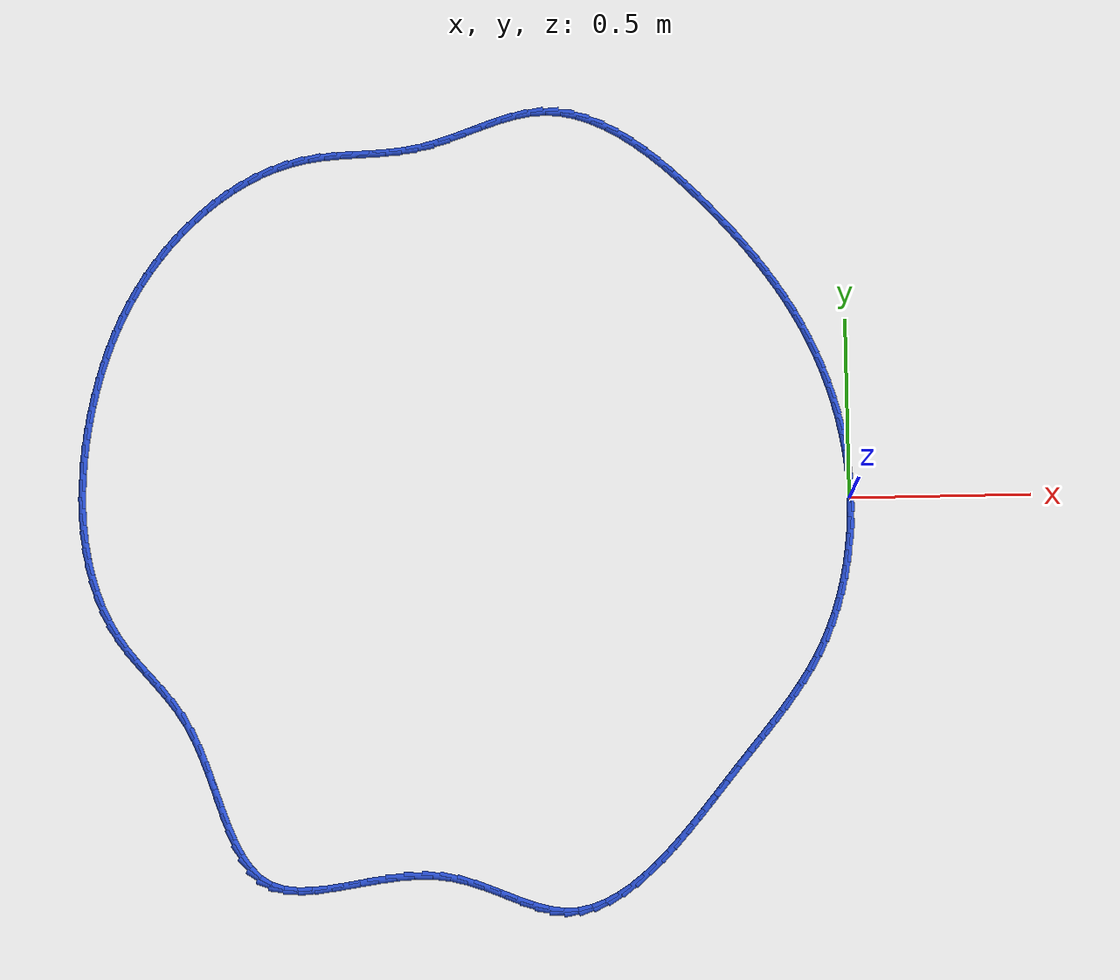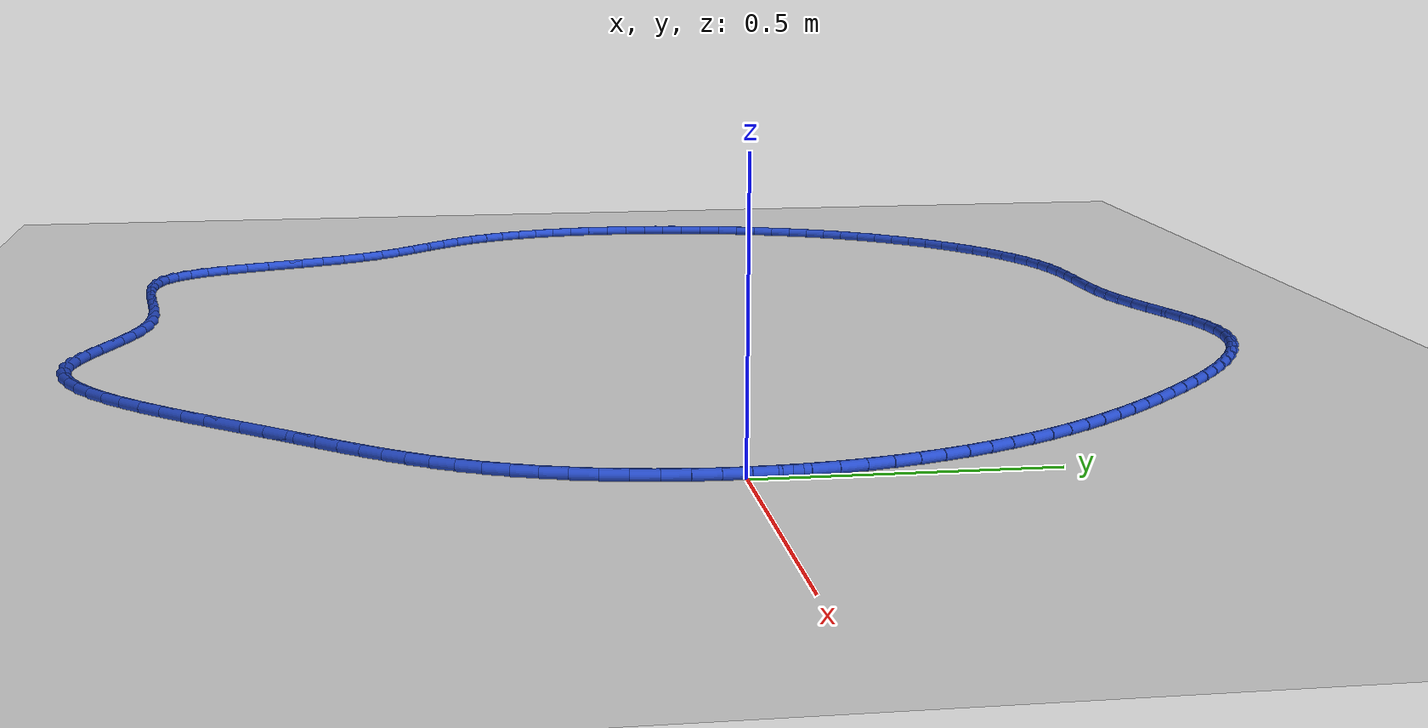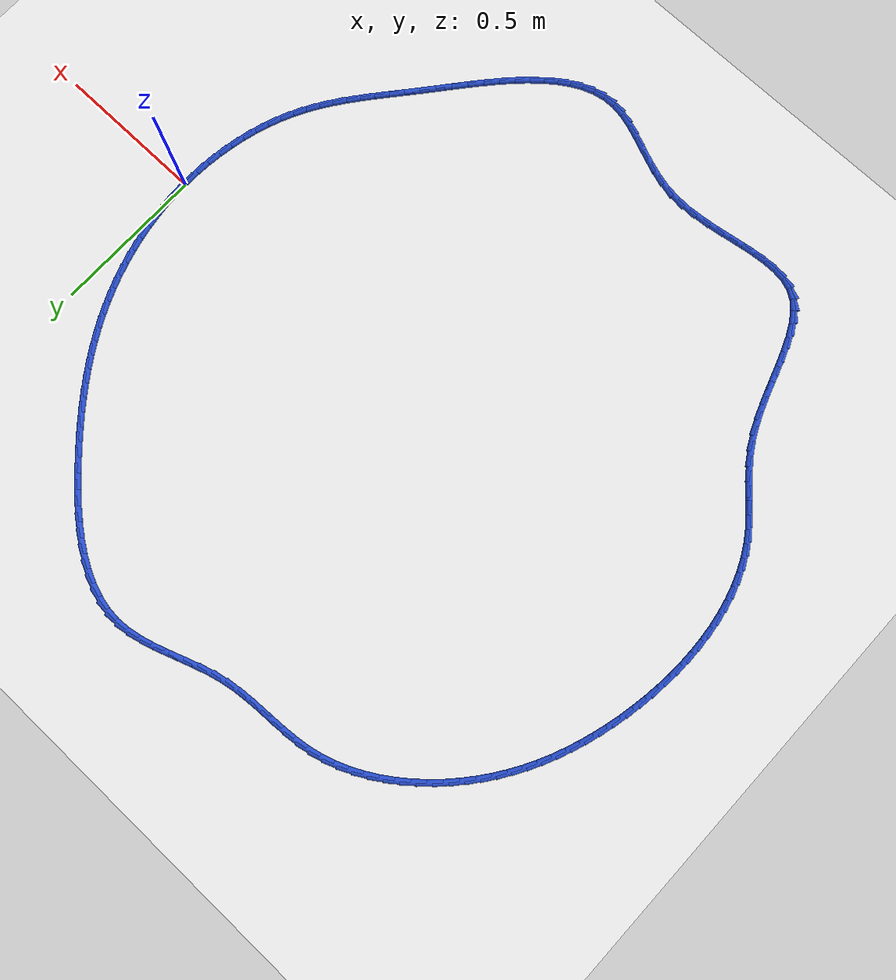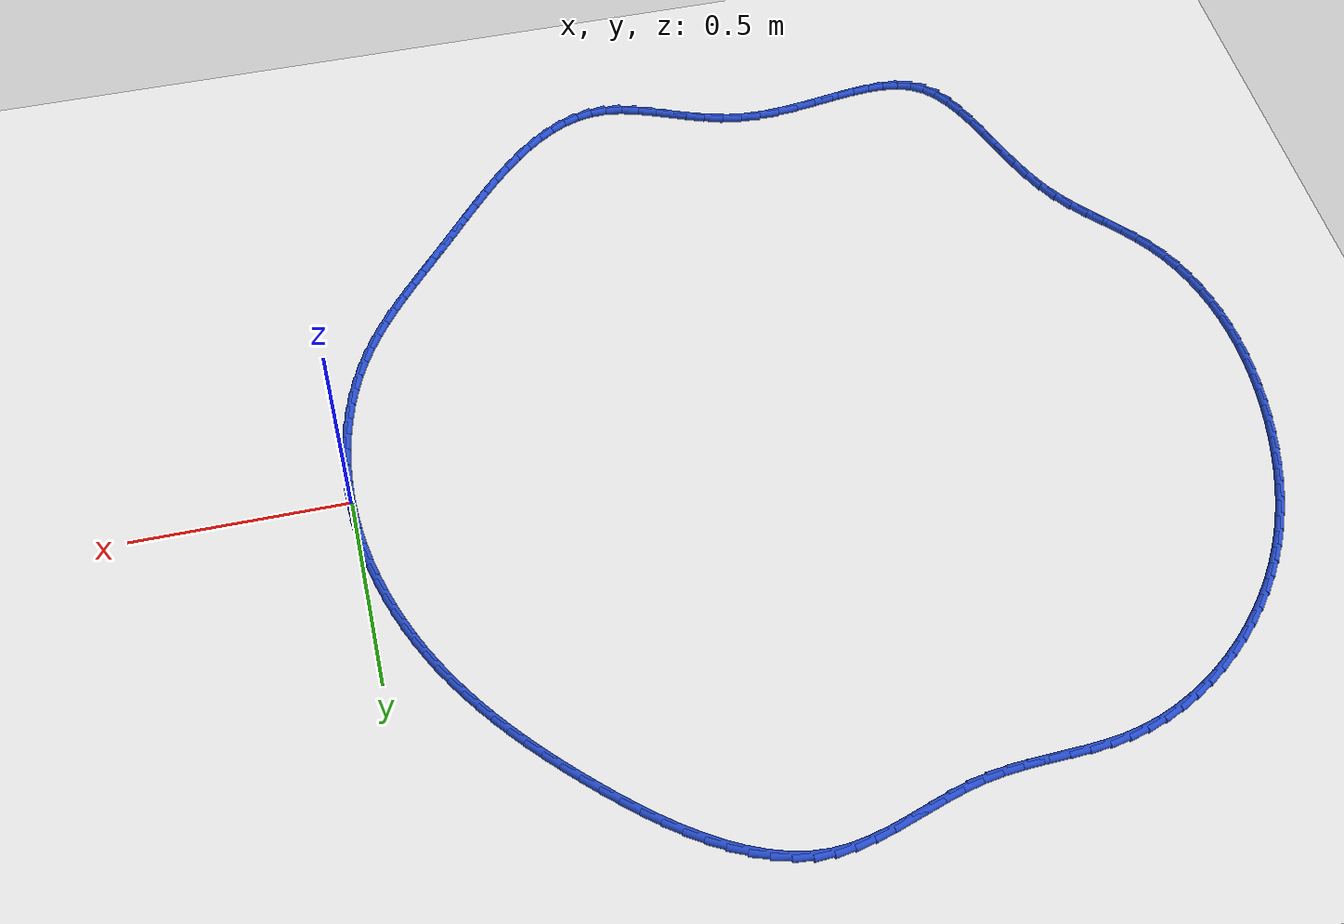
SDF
<sdf version="1.6">
 <world name="default">
  <light name="sun" type="directional">
   <pose>0 0 10 0 -0 0</pose>
   <diffuse>0.8 0.8 0.8 1</diffuse>
   <specular>0.2 0.2 0.2 1</specular>
   <attenuation>
    <range>1000</range>
    <constant>0.9</constant>
    <linear>0.01</linear>
    <quadratic>0.001</quadratic>
   </attenuation>
   <direction>-0.5 0.1 -0.9</direction>
  </light>
  <model name="ground_plane">
   <static>1</static>
   <link name="link">
    <collision name="collision">
     <geometry><plane><normal>0 0 1</normal><size>100 100</size></plane></geometry>
     <surface><friction><ode><mu>100</mu><mu2>50</mu2></ode></friction></surface>
    </collision>
    <visual name="visual">
     <cast_shadows>0</cast_shadows>
     <geometry><plane><normal>0 0 1</normal><size>100 100</size></plane></geometry>
     <material>
      <script><uri>file://media/materials/scripts/gazebo.material</uri><name>Gazebo/WhiteGlow</name></script>
     </material>
    </visual>
   </link>
  </model>
  <gravity>0 0 -9.8</gravity>
  <magnetic_field>6e-06 2.3e-05 -4.2e-05</magnetic_field>
  <atmosphere type="adiabatic"/>
  <physics name="default_physics" default="0" type="ode">
   <max_step_size>0.001</max_step_size>
   <real_time_factor>1</real_time_factor>
   <real_time_update_rate>1000</real_time_update_rate>
  </physics>
  <scene><ambient>0.4 0.4 0.4 1</ambient><background>0.7 0.7 0.7 1</background><shadows>1</shadows></scene>
  <spherical_coordinates>
   <surface_model>EARTH_WGS84</surface_model>
   <latitude_deg>0</latitude_deg>
   <longitude_deg>0</longitude_deg>
   <elevation>0</elevation>
   <heading_deg>0</heading_deg>
  </spherical_coordinates>
  <model name="line">
   <link name="link_0">
    <pose>3.8163916471489756e-17 9.71445146547012e-17 0.01 0 1.57 -1.5379565727730287</pose>
    <collision name="collision">
     <geometry><cylinder><radius>0.01</radius><length>0.08</length></cylinder></geometry>
    </collision>
    <visual name="visual">
     <material>
      <script><name>Gazebo/Blue</name><uri>file://media/materials/scripts/gazebo.material</uri></script>
     </material>
     <geometry><cylinder><radius>0.01</radius><length>0.08</length></cylinder></geometry>
    </visual>
   </link>
   <link name="link_1">
    <pose>-0.0015213505319110554 0.04630983507658337 0.01 0 1.57 -1.4923707919198312</pose>
    <collision name="collision">
     <geometry><cylinder><radius>0.01</radius><length>0.08</length></cylinder></geometry>
    </collision>
    <visual name="visual">
     <material>
      <script><name>Gazebo/Blue</name><uri>file://media/materials/scripts/gazebo.material</uri></script>
     </material>
     <geometry><cylinder><radius>0.01</radius><length>0.08</length></cylinder></geometry>
    </visual>
   </link>
   <link name="link_2">
    <pose>-0.005140305612206082 0.09236030196940077 0.01 0 1.57 -1.4477918984703755</pose>
    <collision name="collision">
     <geometry><cylinder><radius>0.01</radius><length>0.08</length></cylinder></geometry>
    </collision>
    <visual name="visual">
     <material>
      <script><name>Gazebo/Blue</name><uri>file://media/materials/scripts/gazebo.material</uri></script>
     </material>
     <geometry><cylinder><radius>0.01</radius><length>0.08</length></cylinder></geometry>
    </visual>
   </link>
   <link name="link_3">
    <pose>-0.010790470736227298 0.1380630509003677 0.01 0 1.57 -1.4041319630430276</pose>
    <collision name="collision">
     <geometry><cylinder><radius>0.01</radius><length>0.08</length></cylinder></geometry>
    </collision>
    <visual name="visual">
     <material>
      <script><name>Gazebo/Blue</name><uri>file://media/materials/scripts/gazebo.material</uri></script>
     </material>
     <geometry><cylinder><radius>0.01</radius><length>0.08</length></cylinder></geometry>
    </visual>
   </link>
   <link name="link_4">
    <pose>-0.01840545139931693 0.18332973209139947 0.01 0 1.57 -1.3612896721069871</pose>
    <collision name="collision">
     <geometry><cylinder><radius>0.01</radius><length>0.08</length></cylinder></geometry>
    </collision>
    <visual name="visual">
     <material>
      <script><name>Gazebo/Blue</name><uri>file://media/materials/scripts/gazebo.material</uri></script>
     </material>
     <geometry><cylinder><radius>0.01</radius><length>0.08</length></cylinder></geometry>
    </visual>
   </link>
   <link name="link_5">
    <pose>-0.02791885309681721 0.22807199576441128 0.01 0 1.57 -1.3191521934604067</pose>
    <collision name="collision">
     <geometry><cylinder><radius>0.01</radius><length>0.08</length></cylinder></geometry>
    </collision>
    <visual name="visual">
     <material>
      <script><name>Gazebo/Blue</name><uri>file://media/materials/scripts/gazebo.material</uri></script>
     </material>
     <geometry><cylinder><radius>0.01</radius><length>0.08</length></cylinder></geometry>
    </visual>
   </link>
   <link name="link_6">
    <pose>-0.039264281324070435 0.27220149214131867 0.01 0 1.57 -1.2775966391666806</pose>
    <collision name="collision">
     <geometry><cylinder><radius>0.01</radius><length>0.08</length></cylinder></geometry>
    </collision>
    <visual name="visual">
     <material>
      <script><name>Gazebo/Blue</name><uri>file://media/materials/scripts/gazebo.material</uri></script>
     </material>
     <geometry><cylinder><radius>0.01</radius><length>0.08</length></cylinder></geometry>
    </visual>
   </link>
   <link name="link_7">
    <pose>-0.05237534157641881 0.31562987144403687 0.01 0 1.57 -1.2364911311890512</pose>
    <collision name="collision">
     <geometry><cylinder><radius>0.01</radius><length>0.08</length></cylinder></geometry>
    </collision>
    <visual name="visual">
     <material>
      <script><name>Gazebo/Blue</name><uri>file://media/materials/scripts/gazebo.material</uri></script>
     </material>
     <geometry><cylinder><radius>0.01</radius><length>0.08</length></cylinder></geometry>
    </visual>
   </link>
   <link name="link_8">
    <pose>-0.06718563934920459 0.35826878389448125 0.01 0 1.57 -1.1956954917188725</pose>
    <collision name="collision">
     <geometry><cylinder><radius>0.01</radius><length>0.08</length></cylinder></geometry>
    </collision>
    <visual name="visual">
     <material>
      <script><name>Gazebo/Blue</name><uri>file://media/materials/scripts/gazebo.material</uri></script>
     </material>
     <geometry><cylinder><radius>0.01</radius><length>0.08</length></cylinder></geometry>
    </visual>
   </link>
   <link name="link_9">
    <pose>-0.08362878013777 0.40002987971456705 0.01 0 1.57 -1.155131618764823</pose>
    <collision name="collision">
     <geometry><cylinder><radius>0.01</radius><length>0.08</length></cylinder></geometry>
    </collision>
    <visual name="visual">
     <material>
      <script><name>Gazebo/Blue</name><uri>file://media/materials/scripts/gazebo.material</uri></script>
     </material>
     <geometry><cylinder><radius>0.01</radius><length>0.08</length></cylinder></geometry>
    </visual>
   </link>
   <link name="link_10">
    <pose>-0.10164220738040038 0.4408412378524381 0.01 0 1.57 -1.1152504812001924</pose>
    <collision name="collision">
     <geometry><cylinder><radius>0.01</radius><length>0.08</length></cylinder></geometry>
    </collision>
    <visual name="visual">
     <material>
      <script><name>Gazebo/Blue</name><uri>file://media/materials/scripts/gazebo.material</uri></script>
     </material>
     <geometry><cylinder><radius>0.01</radius><length>0.08</length></cylinder></geometry>
    </visual>
   </link>
   <link name="link_11">
    <pose>-0.121188565646555 0.48073881340000635 0.01 0 1.57 -1.0764971303915611</pose>
    <collision name="collision">
     <geometry><cylinder><radius>0.01</radius><length>0.08</length></cylinder></geometry>
    </collision>
    <visual name="visual">
     <material>
      <script><name>Gazebo/Blue</name><uri>file://media/materials/scripts/gazebo.material</uri></script>
     </material>
     <geometry><cylinder><radius>0.01</radius><length>0.08</length></cylinder></geometry>
    </visual>
   </link>
   <link name="link_12">
    <pose>-0.14224066558096513 0.5198020784242768 0.01 0 1.57 -1.0391451640996279</pose>
    <collision name="collision">
     <geometry><cylinder><radius>0.01</radius><length>0.08</length></cylinder></geometry>
    </collision>
    <visual name="visual">
     <material>
      <script><name>Gazebo/Blue</name><uri>file://media/materials/scripts/gazebo.material</uri></script>
     </material>
     <geometry><cylinder><radius>0.01</radius><length>0.08</length></cylinder></geometry>
    </visual>
   </link>
   <link name="link_13">
    <pose>-0.16477134600680102 0.5581106256130831 0.01 0 1.57 -1.0034326714156125</pose>
    <collision name="collision">
     <geometry><cylinder><radius>0.01</radius><length>0.08</length></cylinder></geometry>
    </collision>
    <visual name="visual">
     <material>
      <script><name>Gazebo/Blue</name><uri>file://media/materials/scripts/gazebo.material</uri></script>
     </material>
     <geometry><cylinder><radius>0.01</radius><length>0.08</length></cylinder></geometry>
    </visual>
   </link>
   <link name="link_14">
    <pose>-0.1887534457472327 0.5957440476542584 0.01 0 1.57 -0.9695582686002274</pose>
    <collision name="collision">
     <geometry><cylinder><radius>0.01</radius><length>0.08</length></cylinder></geometry>
    </collision>
    <visual name="visual">
     <material>
      <script><name>Gazebo/Blue</name><uri>file://media/materials/scripts/gazebo.material</uri></script>
     </material>
     <geometry><cylinder><radius>0.01</radius><length>0.08</length></cylinder></geometry>
    </visual>
   </link>
   <link name="link_15">
    <pose>-0.21415980362543027 0.6327819372356356 0.01 0 1.57 -0.93767916767748</pose>
    <collision name="collision">
     <geometry><cylinder><radius>0.01</radius><length>0.08</length></cylinder></geometry>
    </collision>
    <visual name="visual">
     <material>
      <script><name>Gazebo/Blue</name><uri>file://media/materials/scripts/gazebo.material</uri></script>
     </material>
     <geometry><cylinder><radius>0.01</radius><length>0.08</length></cylinder></geometry>
    </visual>
   </link>
   <link name="link_16">
    <pose>-0.2409632584645639 0.6693038870450483 0.01 0 1.57 -0.9079115399007249</pose>
    <collision name="collision">
     <geometry><cylinder><radius>0.01</radius><length>0.08</length></cylinder></geometry>
    </collision>
    <visual name="visual">
     <material>
      <script><name>Gazebo/Blue</name><uri>file://media/materials/scripts/gazebo.material</uri></script>
     </material>
     <geometry><cylinder><radius>0.01</radius><length>0.08</length></cylinder></geometry>
    </visual>
   </link>
   <link name="link_17">
    <pose>-0.26913664908780366 0.7053894897703294 0.01 0 1.57 -0.8803327407412849</pose>
    <collision name="collision">
     <geometry><cylinder><radius>0.01</radius><length>0.08</length></cylinder></geometry>
    </collision>
    <visual name="visual">
     <material>
      <script><name>Gazebo/Blue</name><uri>file://media/materials/scripts/gazebo.material</uri></script>
     </material>
     <geometry><cylinder><radius>0.01</radius><length>0.08</length></cylinder></geometry>
    </visual>
   </link>
   <link name="link_18">
    <pose>-0.2986528143183197 0.7411183380993126 0.01 0 1.57 -0.854984877392644</pose>
    <collision name="collision">
     <geometry><cylinder><radius>0.01</radius><length>0.08</length></cylinder></geometry>
    </collision>
    <visual name="visual">
     <material>
      <script><name>Gazebo/Blue</name><uri>file://media/materials/scripts/gazebo.material</uri></script>
     </material>
     <geometry><cylinder><radius>0.01</radius><length>0.08</length></cylinder></geometry>
    </visual>
   </link>
   <link name="link_19">
    <pose>-0.32948459297928206 0.7765700247198306 0.01 0 1.57 -0.8318791984274541</pose>
    <collision name="collision">
     <geometry><cylinder><radius>0.01</radius><length>0.08</length></cylinder></geometry>
    </collision>
    <visual name="visual">
     <material>
      <script><name>Gazebo/Blue</name><uri>file://media/materials/scripts/gazebo.material</uri></script>
     </material>
     <geometry><cylinder><radius>0.01</radius><length>0.08</length></cylinder></geometry>
    </visual>
   </link>
   <link name="link_20">
    <pose>-0.361604823893861 0.811824142319717 0.01 0 1.57 -0.8109976034258556</pose>
    <collision name="collision">
     <geometry><cylinder><radius>0.01</radius><length>0.08</length></cylinder></geometry>
    </collision>
    <visual name="visual">
     <material>
      <script><name>Gazebo/Blue</name><uri>file://media/materials/scripts/gazebo.material</uri></script>
     </material>
     <geometry><cylinder><radius>0.01</radius><length>0.08</length></cylinder></geometry>
    </visual>
   </link>
   <link name="link_21">
    <pose>-0.3949863238192327 0.8469600323115121 0.01 0 1.57 -0.7903148346299953</pose>
    <collision name="collision">
     <geometry><cylinder><radius>0.01</radius><length>0.08</length></cylinder></geometry>
    </collision>
    <visual name="visual">
     <material>
      <script><name>Gazebo/Blue</name><uri>file://media/materials/scripts/gazebo.material</uri></script>
     </material>
     <geometry><cylinder><radius>0.01</radius><length>0.08</length></cylinder></geometry>
    </visual>
   </link>
   <link name="link_22">
    <pose>-0.4295884818337437 0.8819041291519079 0.01 0 1.57 -0.7642693965937991</pose>
    <collision name="collision">
     <geometry><cylinder><radius>0.01</radius><length>0.08</length></cylinder></geometry>
    </collision>
    <visual name="visual">
     <material>
      <script><name>Gazebo/Blue</name><uri>file://media/materials/scripts/gazebo.material</uri></script>
     </material>
     <geometry><cylinder><radius>0.01</radius><length>0.08</length></cylinder></geometry>
    </visual>
   </link>
   <link name="link_23">
    <pose>-0.4653344864729322 0.9161706356028285 0.01 0 1.57 -0.7314331395945434</pose>
    <collision name="collision">
     <geometry><cylinder><radius>0.01</radius><length>0.08</length></cylinder></geometry>
    </collision>
    <visual name="visual">
     <material>
      <script><name>Gazebo/Blue</name><uri>file://media/materials/scripts/gazebo.material</uri></script>
     </material>
     <geometry><cylinder><radius>0.01</radius><length>0.08</length></cylinder></geometry>
    </visual>
   </link>
   <link name="link_24">
    <pose>-0.5021414870566503 0.9492049831889705 0.01 0 1.57 -0.6909779815725277</pose>
    <collision name="collision">
     <geometry><cylinder><radius>0.01</radius><length>0.08</length></cylinder></geometry>
    </collision>
    <visual name="visual">
     <material>
      <script><name>Gazebo/Blue</name><uri>file://media/materials/scripts/gazebo.material</uri></script>
     </material>
     <geometry><cylinder><radius>0.01</radius><length>0.08</length></cylinder></geometry>
    </visual>
   </link>
   <link name="link_25">
    <pose>-0.5399266329047504 0.9804526034350306 0.01 0 1.57 -0.6417780227426142</pose>
    <collision name="collision">
     <geometry><cylinder><radius>0.01</radius><length>0.08</length></cylinder></geometry>
    </collision>
    <visual name="visual">
     <material>
      <script><name>Gazebo/Blue</name><uri>file://media/materials/scripts/gazebo.material</uri></script>
     </material>
     <geometry><cylinder><radius>0.01</radius><length>0.08</length></cylinder></geometry>
    </visual>
   </link>
   <link name="link_26">
    <pose>-0.5786070733370846 1.0093589278657045 0.01 0 1.57 -0.5824050629398242</pose>
    <collision name="collision">
     <geometry><cylinder><radius>0.01</radius><length>0.08</length></cylinder></geometry>
    </collision>
    <visual name="visual">
     <material>
      <script><name>Gazebo/Blue</name><uri>file://media/materials/scripts/gazebo.material</uri></script>
     </material>
     <geometry><cylinder><radius>0.01</radius><length>0.08</length></cylinder></geometry>
    </visual>
   </link>
   <link name="link_27">
    <pose>-0.6180999576735055 1.0353693880056891 0.01 0 1.57 -0.5111588204902087</pose>
    <collision name="collision">
     <geometry><cylinder><radius>0.01</radius><length>0.08</length></cylinder></geometry>
    </collision>
    <visual name="visual">
     <material>
      <script><name>Gazebo/Blue</name><uri>file://media/materials/scripts/gazebo.material</uri></script>
     </material>
     <geometry><cylinder><radius>0.01</radius><length>0.08</length></cylinder></geometry>
    </visual>
   </link>
   <link name="link_28">
    <pose>-0.658322435233865 1.0579294153796812 0.01 0 1.57 -0.42618346433243837</pose>
    <collision name="collision">
     <geometry><cylinder><radius>0.01</radius><length>0.08</length></cylinder></geometry>
    </collision>
    <visual name="visual">
     <material>
      <script><name>Gazebo/Blue</name><uri>file://media/materials/scripts/gazebo.material</uri></script>
     </material>
     <geometry><cylinder><radius>0.01</radius><length>0.08</length></cylinder></geometry>
    </visual>
   </link>
   <link name="link_29">
    <pose>-0.6991916553380156 1.0764844415123764 0.01 0 1.57 -0.3257510978712174</pose>
    <collision name="collision">
     <geometry><cylinder><radius>0.01</radius><length>0.08</length></cylinder></geometry>
    </collision>
    <visual name="visual">
     <material>
      <script><name>Gazebo/Blue</name><uri>file://media/materials/scripts/gazebo.material</uri></script>
     </material>
     <geometry><cylinder><radius>0.01</radius><length>0.08</length></cylinder></geometry>
    </visual>
   </link>
   <link name="link_30">
    <pose>-0.7406247673058097 1.0904798979284718 0.01 0 1.57 -0.2088046056208526</pose>
    <collision name="collision">
     <geometry><cylinder><radius>0.01</radius><length>0.08</length></cylinder></geometry>
    </collision>
    <visual name="visual">
     <material>
      <script><name>Gazebo/Blue</name><uri>file://media/materials/scripts/gazebo.material</uri></script>
     </material>
     <geometry><cylinder><radius>0.01</radius><length>0.08</length></cylinder></geometry>
    </visual>
   </link>
   <link name="link_31">
    <pose>-0.7825389204570993 1.0993612161526634 0.01 0 1.57 -0.07578071122685932</pose>
    <collision name="collision">
     <geometry><cylinder><radius>0.01</radius><length>0.08</length></cylinder></geometry>
    </collision>
    <visual name="visual">
     <material>
      <script><name>Gazebo/Blue</name><uri>file://media/materials/scripts/gazebo.material</uri></script>
     </material>
     <geometry><cylinder><radius>0.01</radius><length>0.08</length></cylinder></geometry>
    </visual>
   </link>
   <link name="link_32">
    <pose>-0.8248512641117365 1.1025738277096475 0.01 0 1.57 0.06569908079968896</pose>
    <collision name="collision">
     <geometry><cylinder><radius>0.01</radius><length>0.08</length></cylinder></geometry>
    </collision>
    <visual name="visual">
     <material>
      <script><name>Gazebo/Blue</name><uri>file://media/materials/scripts/gazebo.material</uri></script>
     </material>
     <geometry><cylinder><radius>0.01</radius><length>0.08</length></cylinder></geometry>
    </visual>
   </link>
   <link name="link_33">
    <pose>-0.8674887890774303 1.099768544136677 0.01 0 1.57 0.18326894794914236</pose>
    <collision name="collision">
     <geometry><cylinder><radius>0.01</radius><length>0.08</length></cylinder></geometry>
    </collision>
    <visual name="visual">
     <material>
      <script><name>Gazebo/Blue</name><uri>file://media/materials/scripts/gazebo.material</uri></script>
     </material>
     <geometry><cylinder><radius>0.01</radius><length>0.08</length></cylinder></geometry>
    </visual>
   </link>
   <link name="link_34">
    <pose>-0.9104365657303468 1.0918082276968315 0.01 0 1.57 0.26646832312876595</pose>
    <collision name="collision">
     <geometry><cylinder><radius>0.01</radius><length>0.08</length></cylinder></geometry>
    </collision>
    <visual name="visual">
     <material>
      <script><name>Gazebo/Blue</name><uri>file://media/materials/scripts/gazebo.material</uri></script>
     </material>
     <geometry><cylinder><radius>0.01</radius><length>0.08</length></cylinder></geometry>
    </visual>
   </link>
   <link name="link_35">
    <pose>-0.9537008957044704 1.0799988114633285 0.01 0 1.57 0.3180883479107119</pose>
    <collision name="collision">
     <geometry><cylinder><radius>0.01</radius><length>0.08</length></cylinder></geometry>
    </collision>
    <visual name="visual">
     <material>
      <script><name>Gazebo/Blue</name><uri>file://media/materials/scripts/gazebo.material</uri></script>
     </material>
     <geometry><cylinder><radius>0.01</radius><length>0.08</length></cylinder></geometry>
    </visual>
   </link>
   <link name="link_36">
    <pose>-0.9972881121115185 1.06564688541178 0.01 0 1.57 0.34107186855358246</pose>
    <collision name="collision">
     <geometry><cylinder><radius>0.01</radius><length>0.08</length></cylinder></geometry>
    </collision>
    <visual name="visual">
     <material>
      <script><name>Gazebo/Blue</name><uri>file://media/materials/scripts/gazebo.material</uri></script>
     </material>
     <geometry><cylinder><radius>0.01</radius><length>0.08</length></cylinder></geometry>
    </visual>
   </link>
   <link name="link_37">
    <pose>-1.041204548063207 1.050059039517797 0.01 0 1.57 0.3372581123567718</pose>
    <collision name="collision">
     <geometry><cylinder><radius>0.01</radius><length>0.08</length></cylinder></geometry>
    </collision>
    <visual name="visual">
     <material>
      <script><name>Gazebo/Blue</name><uri>file://media/materials/scripts/gazebo.material</uri></script>
     </material>
     <geometry><cylinder><radius>0.01</radius><length>0.08</length></cylinder></geometry>
    </visual>
   </link>
   <link name="link_38">
    <pose>-1.085456536671253 1.0345418637569912 0.01 0 1.57 0.30705377053504007</pose>
    <collision name="collision">
     <geometry><cylinder><radius>0.01</radius><length>0.08</length></cylinder></geometry>
    </collision>
    <visual name="visual">
     <material>
      <script><name>Gazebo/Blue</name><uri>file://media/materials/scripts/gazebo.material</uri></script>
     </material>
     <geometry><cylinder><radius>0.01</radius><length>0.08</length></cylinder></geometry>
    </visual>
   </link>
   <link name="link_39">
    <pose>-1.1300504110473726 1.0204019481049733 0.01 0 1.57 0.24959189542586935</pose>
    <collision name="collision">
     <geometry><cylinder><radius>0.01</radius><length>0.08</length></cylinder></geometry>
    </collision>
    <visual name="visual">
     <material>
      <script><name>Gazebo/Blue</name><uri>file://media/materials/scripts/gazebo.material</uri></script>
     </material>
     <geometry><cylinder><radius>0.01</radius><length>0.08</length></cylinder></geometry>
    </visual>
   </link>
   <link name="link_40">
    <pose>-1.1749925043032832 1.008945882537356 0.01 0 1.57 0.1698947916991378</pose>
    <collision name="collision">
     <geometry><cylinder><radius>0.01</radius><length>0.08</length></cylinder></geometry>
    </collision>
    <visual name="visual">
     <material>
      <script><name>Gazebo/Blue</name><uri>file://media/materials/scripts/gazebo.material</uri></script>
     </material>
     <geometry><cylinder><radius>0.01</radius><length>0.08</length></cylinder></geometry>
    </visual>
   </link>
   <link name="link_41">
    <pose>-1.220270551940147 1.0011785006691818 0.01 0 1.57 0.10242214928753134</pose>
    <collision name="collision">
     <geometry><cylinder><radius>0.01</radius><length>0.08</length></cylinder></geometry>
    </collision>
    <visual name="visual">
     <material>
      <script><name>Gazebo/Blue</name><uri>file://media/materials/scripts/gazebo.material</uri></script>
     </material>
     <geometry><cylinder><radius>0.01</radius><length>0.08</length></cylinder></geometry>
    </visual>
   </link>
   <link name="link_42">
    <pose>-1.2657734940110714 0.9965016261610742 0.01 0 1.57 0.059485050405694025</pose>
    <collision name="collision">
     <geometry><cylinder><radius>0.01</radius><length>0.08</length></cylinder></geometry>
    </collision>
    <visual name="visual">
     <material>
      <script><name>Gazebo/Blue</name><uri>file://media/materials/scripts/gazebo.material</uri></script>
     </material>
     <geometry><cylinder><radius>0.01</radius><length>0.08</length></cylinder></geometry>
    </visual>
   </link>
   <link name="link_43">
    <pose>-1.31135759174807 0.9937868510026211 0.01 0 1.57 0.041306899622353586</pose>
    <collision name="collision">
     <geometry><cylinder><radius>0.01</radius><length>0.08</length></cylinder></geometry>
    </collision>
    <visual name="visual">
     <material>
      <script><name>Gazebo/Blue</name><uri>file://media/materials/scripts/gazebo.material</uri></script>
     </material>
     <geometry><cylinder><radius>0.01</radius><length>0.08</length></cylinder></geometry>
    </visual>
   </link>
   <link name="link_44">
    <pose>-1.356879085543031 0.991905429041048 0.01 0 1.57 0.04800036609198862</pose>
    <collision name="collision">
     <geometry><cylinder><radius>0.01</radius><length>0.08</length></cylinder></geometry>
    </collision>
    <visual name="visual">
     <material>
      <script><name>Gazebo/Blue</name><uri>file://media/materials/scripts/gazebo.material</uri></script>
     </material>
     <geometry><cylinder><radius>0.01</radius><length>0.08</length></cylinder></geometry>
    </visual>
   </link>
   <link name="link_45">
    <pose>-1.4021942157878446 0.989728614123581 0.01 0 1.57 0.07991292943495168</pose>
    <collision name="collision">
     <geometry><cylinder><radius>0.01</radius><length>0.08</length></cylinder></geometry>
    </collision>
    <visual name="visual">
     <material>
      <script><name>Gazebo/Blue</name><uri>file://media/materials/scripts/gazebo.material</uri></script>
     </material>
     <geometry><cylinder><radius>0.01</radius><length>0.08</length></cylinder></geometry>
    </visual>
   </link>
   <link name="link_46">
    <pose>-1.4471592228743986 0.9861276600974459 0.01 0 1.57 0.13750507843735582</pose>
    <collision name="collision">
     <geometry><cylinder><radius>0.01</radius><length>0.08</length></cylinder></geometry>
    </collision>
    <visual name="visual">
     <material>
      <script><name>Gazebo/Blue</name><uri>file://media/materials/scripts/gazebo.material</uri></script>
     </material>
     <geometry><cylinder><radius>0.01</radius><length>0.08</length></cylinder></geometry>
    </visual>
   </link>
   <link name="link_47">
    <pose>-1.4916303471945824 0.9799738208098688 0.01 0 1.57 0.21924860258075093</pose>
    <collision name="collision">
     <geometry><cylinder><radius>0.01</radius><length>0.08</length></cylinder></geometry>
    </collision>
    <visual name="visual">
     <material>
      <script><name>Gazebo/Blue</name><uri>file://media/materials/scripts/gazebo.material</uri></script>
     </material>
     <geometry><cylinder><radius>0.01</radius><length>0.08</length></cylinder></geometry>
    </visual>
   </link>
   <link name="link_48">
    <pose>-1.5354640097102266 0.9702063402634762 0.01 0 1.57 0.3067010706615668</pose>
    <collision name="collision">
     <geometry><cylinder><radius>0.01</radius><length>0.08</length></cylinder></geometry>
    </collision>
    <visual name="visual">
     <material>
      <script><name>Gazebo/Blue</name><uri>file://media/materials/scripts/gazebo.material</uri></script>
     </material>
     <geometry><cylinder><radius>0.01</radius><length>0.08</length></cylinder></geometry>
    </visual>
   </link>
   <link name="link_49">
    <pose>-1.5785187738280961 0.9565711590953223 0.01 0 1.57 0.38814090605224666</pose>
    <collision name="collision">
     <geometry><cylinder><radius>0.01</radius><length>0.08</length></cylinder></geometry>
    </collision>
    <visual name="visual">
     <material>
      <script><name>Gazebo/Blue</name><uri>file://media/materials/scripts/gazebo.material</uri></script>
     </material>
     <geometry><cylinder><radius>0.01</radius><length>0.08</length></cylinder></geometry>
    </visual>
   </link>
   <link name="link_50">
    <pose>-1.6206546060291915 0.939342518690705 0.01 0 1.57 0.46365244157971647</pose>
    <collision name="collision">
     <geometry><cylinder><radius>0.01</radius><length>0.08</length></cylinder></geometry>
    </collision>
    <visual name="visual">
     <material>
      <script><name>Gazebo/Blue</name><uri>file://media/materials/scripts/gazebo.material</uri></script>
     </material>
     <geometry><cylinder><radius>0.01</radius><length>0.08</length></cylinder></geometry>
    </visual>
   </link>
   <link name="link_51">
    <pose>-1.6617314971339991 0.9188038250035545 0.01 0 1.57 0.5337286970925009</pose>
    <collision name="collision">
     <geometry><cylinder><radius>0.01</radius><length>0.08</length></cylinder></geometry>
    </collision>
    <visual name="visual">
     <material>
      <script><name>Gazebo/Blue</name><uri>file://media/materials/scripts/gazebo.material</uri></script>
     </material>
     <geometry><cylinder><radius>0.01</radius><length>0.08</length></cylinder></geometry>
    </visual>
   </link>
   <link name="link_52">
    <pose>-1.701609437963006 0.8952384839878004 0.01 0 1.57 0.5989855732832398</pose>
    <collision name="collision">
     <geometry><cylinder><radius>0.01</radius><length>0.08</length></cylinder></geometry>
    </collision>
    <visual name="visual">
     <material>
      <script><name>Gazebo/Blue</name><uri>file://media/materials/scripts/gazebo.material</uri></script>
     </material>
     <geometry><cylinder><radius>0.01</radius><length>0.08</length></cylinder></geometry>
    </visual>
   </link>
   <link name="link_53">
    <pose>-1.740148419336701 0.8689299015973732 0.01 0 1.57 0.6601003556676743</pose>
    <collision name="collision">
     <geometry><cylinder><radius>0.01</radius><length>0.08</length></cylinder></geometry>
    </collision>
    <visual name="visual">
     <material>
      <script><name>Gazebo/Blue</name><uri>file://media/materials/scripts/gazebo.material</uri></script>
     </material>
     <geometry><cylinder><radius>0.01</radius><length>0.08</length></cylinder></geometry>
    </visual>
   </link>
   <link name="link_54">
    <pose>-1.7772084320755717 0.840161483786202 0.01 0 1.57 0.717773368047106</pose>
    <collision name="collision">
     <geometry><cylinder><radius>0.01</radius><length>0.08</length></cylinder></geometry>
    </collision>
    <visual name="visual">
     <material>
      <script><name>Gazebo/Blue</name><uri>file://media/materials/scripts/gazebo.material</uri></script>
     </material>
     <geometry><cylinder><radius>0.01</radius><length>0.08</length></cylinder></geometry>
    </visual>
   </link>
   <link name="link_55">
    <pose>-1.812649467000106 0.8092166365082181 0.01 0 1.57 0.7727082527381874</pose>
    <collision name="collision">
     <geometry><cylinder><radius>0.01</radius><length>0.08</length></cylinder></geometry>
    </collision>
    <visual name="visual">
     <material>
      <script><name>Gazebo/Blue</name><uri>file://media/materials/scripts/gazebo.material</uri></script>
     </material>
     <geometry><cylinder><radius>0.01</radius><length>0.08</length></cylinder></geometry>
    </visual>
   </link>
   <link name="link_56">
    <pose>-1.846331514930791 0.7763787657173508 0.01 0 1.57 0.8256062091136608</pose>
    <collision name="collision">
     <geometry><cylinder><radius>0.01</radius><length>0.08</length></cylinder></geometry>
    </collision>
    <visual name="visual">
     <material>
      <script><name>Gazebo/Blue</name><uri>file://media/materials/scripts/gazebo.material</uri></script>
     </material>
     <geometry><cylinder><radius>0.01</radius><length>0.08</length></cylinder></geometry>
    </visual>
   </link>
   <link name="link_57">
    <pose>-1.8781145666881147 0.74193127736753 0.01 0 1.57 0.8771704968651995</pose>
    <collision name="collision">
     <geometry><cylinder><radius>0.01</radius><length>0.08</length></cylinder></geometry>
    </collision>
    <visual name="visual">
     <material>
      <script><name>Gazebo/Blue</name><uri>file://media/materials/scripts/gazebo.material</uri></script>
     </material>
     <geometry><cylinder><radius>0.01</radius><length>0.08</length></cylinder></geometry>
    </visual>
   </link>
   <link name="link_58">
    <pose>-1.9078586130925652 0.7061575774126857 0.01 0 1.57 0.9281133519541436</pose>
    <collision name="collision">
     <geometry><cylinder><radius>0.01</radius><length>0.08</length></cylinder></geometry>
    </collision>
    <visual name="visual">
     <material>
      <script><name>Gazebo/Blue</name><uri>file://media/materials/scripts/gazebo.material</uri></script>
     </material>
     <geometry><cylinder><radius>0.01</radius><length>0.08</length></cylinder></geometry>
    </visual>
   </link>
   <link name="link_59">
    <pose>-1.935438166939372 0.6693220933533235 0.01 0 1.57 0.9788016310542917</pose>
    <collision name="collision">
     <geometry><cylinder><radius>0.01</radius><length>0.08</length></cylinder></geometry>
    </collision>
    <visual name="visual">
     <material>
      <script><name>Gazebo/Blue</name><uri>file://media/materials/scripts/gazebo.material</uri></script>
     </material>
     <geometry><cylinder><radius>0.01</radius><length>0.08</length></cylinder></geometry>
    </visual>
   </link>
   <link name="link_60">
    <pose>-1.9608644741562067 0.6315105591285235 0.01 0 1.57 1.028873572069799</pose>
    <collision name="collision">
     <geometry><cylinder><radius>0.01</radius><length>0.08</length></cylinder></geometry>
    </collision>
    <visual name="visual">
     <material>
      <script><name>Gazebo/Blue</name><uri>file://media/materials/scripts/gazebo.material</uri></script>
     </material>
     <geometry><cylinder><radius>0.01</radius><length>0.08</length></cylinder></geometry>
    </visual>
   </link>
   <link name="link_61">
    <pose>-1.9842238201040465 0.5927106412715716 0.01 0 1.57 1.0778724670143625</pose>
    <collision name="collision">
     <geometry><cylinder><radius>0.01</radius><length>0.08</length></cylinder></geometry>
    </collision>
    <visual name="visual">
     <material>
      <script><name>Gazebo/Blue</name><uri>file://media/materials/scripts/gazebo.material</uri></script>
     </material>
     <geometry><cylinder><radius>0.01</radius><length>0.08</length></cylinder></geometry>
    </visual>
   </link>
   <link name="link_62">
    <pose>-2.0056032628900584 0.5529089964305387 0.01 0 1.57 1.1253777031563543</pose>
    <collision name="collision">
     <geometry><cylinder><radius>0.01</radius><length>0.08</length></cylinder></geometry>
    </collision>
    <visual name="visual">
     <material>
      <script><name>Gazebo/Blue</name><uri>file://media/materials/scripts/gazebo.material</uri></script>
     </material>
     <geometry><cylinder><radius>0.01</radius><length>0.08</length></cylinder></geometry>
    </visual>
   </link>
   <link name="link_63">
    <pose>-2.0250898606214083 0.5120922812534954 0.01 0 1.57 1.171019883879433</pose>
    <collision name="collision">
     <geometry><cylinder><radius>0.01</radius><length>0.08</length></cylinder></geometry>
    </collision>
    <visual name="visual">
     <material>
      <script><name>Gazebo/Blue</name><uri>file://media/materials/scripts/gazebo.material</uri></script>
     </material>
     <geometry><cylinder><radius>0.01</radius><length>0.08</length></cylinder></geometry>
    </visual>
   </link>
   <link name="link_64">
    <pose>-2.0427706714052647 0.47024715238851267 0.01 0 1.57 1.2144912479256051</pose>
    <collision name="collision">
     <geometry><cylinder><radius>0.01</radius><length>0.08</length></cylinder></geometry>
    </collision>
    <visual name="visual">
     <material>
      <script><name>Gazebo/Blue</name><uri>file://media/materials/scripts/gazebo.material</uri></script>
     </material>
     <geometry><cylinder><radius>0.01</radius><length>0.08</length></cylinder></geometry>
    </visual>
   </link>
   <link name="link_65">
    <pose>-2.058732753348795 0.4273602664836611 0.01 0 1.57 1.2555507181265897</pose>
    <collision name="collision">
     <geometry><cylinder><radius>0.01</radius><length>0.08</length></cylinder></geometry>
    </collision>
    <visual name="visual">
     <material>
      <script><name>Gazebo/Blue</name><uri>file://media/materials/scripts/gazebo.material</uri></script>
     </material>
     <geometry><cylinder><radius>0.01</radius><length>0.08</length></cylinder></geometry>
    </visual>
   </link>
   <link name="link_66">
    <pose>-2.0730631645591644 0.38341828018701124 0.01 0 1.57 1.2940280527197485</pose>
    <collision name="collision">
     <geometry><cylinder><radius>0.01</radius><length>0.08</length></cylinder></geometry>
    </collision>
    <visual name="visual">
     <material>
      <script><name>Gazebo/Blue</name><uri>file://media/materials/scripts/gazebo.material</uri></script>
     </material>
     <geometry><cylinder><radius>0.01</radius><length>0.08</length></cylinder></geometry>
    </visual>
   </link>
   <link name="link_67">
    <pose>-2.085848672174367 0.338408176515621 0.01 0 1.57 1.3306575052550618</pose>
    <collision name="collision">
     <geometry><cylinder><radius>0.01</radius><length>0.08</length></cylinder></geometry>
    </collision>
    <visual name="visual">
     <material>
      <script><name>Gazebo/Blue</name><uri>file://media/materials/scripts/gazebo.material</uri></script>
     </material>
     <geometry><cylinder><radius>0.01</radius><length>0.08</length></cylinder></geometry>
    </visual>
   </link>
   <link name="link_68">
    <pose>-2.0971191139227865 0.2923807940262099 0.01 0 1.57 1.3674630871520572</pose>
    <collision name="collision">
     <geometry><cylinder><radius>0.01</radius><length>0.08</length></cylinder></geometry>
    </collision>
    <visual name="visual">
     <material>
      <script><name>Gazebo/Blue</name><uri>file://media/materials/scripts/gazebo.material</uri></script>
     </material>
     <geometry><cylinder><radius>0.01</radius><length>0.08</length></cylinder></geometry>
    </visual>
   </link>
   <link name="link_69">
    <pose>-2.1067795703183667 0.2455269066675874 0.01 0 1.57 1.4050908066854757</pose>
    <collision name="collision">
     <geometry><cylinder><radius>0.01</radius><length>0.08</length></cylinder></geometry>
    </collision>
    <visual name="visual">
     <material>
      <script><name>Gazebo/Blue</name><uri>file://media/materials/scripts/gazebo.material</uri></script>
     </material>
     <geometry><cylinder><radius>0.01</radius><length>0.08</length></cylinder></geometry>
    </visual>
   </link>
   <link name="link_70">
    <pose>-2.1147185861732027 0.19805583585238865 0.01 0 1.57 1.4439485734308788</pose>
    <collision name="collision">
     <geometry><cylinder><radius>0.01</radius><length>0.08</length></cylinder></geometry>
    </collision>
    <visual name="visual">
     <material>
      <script><name>Gazebo/Blue</name><uri>file://media/materials/scripts/gazebo.material</uri></script>
     </material>
     <geometry><cylinder><radius>0.01</radius><length>0.08</length></cylinder></geometry>
    </visual>
   </link>
   <link name="link_71">
    <pose>-2.120824706299389 0.15017690299324865 0.01 0 1.57 1.484447767332072</pose>
    <collision name="collision">
     <geometry><cylinder><radius>0.01</radius><length>0.08</length></cylinder></geometry>
    </collision>
    <visual name="visual">
     <material>
      <script><name>Gazebo/Blue</name><uri>file://media/materials/scripts/gazebo.material</uri></script>
     </material>
     <geometry><cylinder><radius>0.01</radius><length>0.08</length></cylinder></geometry>
    </visual>
   </link>
   <link name="link_72">
    <pose>-2.1249864755090204 0.10209942950280348 0.01 0 1.57 1.5270109736996424</pose>
    <collision name="collision">
     <geometry><cylinder><radius>0.01</radius><length>0.08</length></cylinder></geometry>
    </collision>
    <visual name="visual">
     <material>
      <script><name>Gazebo/Blue</name><uri>file://media/materials/scripts/gazebo.material</uri></script>
     </material>
     <geometry><cylinder><radius>0.01</radius><length>0.08</length></cylinder></geometry>
    </visual>
   </link>
   <link name="link_73">
    <pose>-2.12709243861419 0.054032736793688085 0.01 0 1.57 -1.5695151873657478</pose>
    <collision name="collision">
     <geometry><cylinder><radius>0.01</radius><length>0.08</length></cylinder></geometry>
    </collision>
    <visual name="visual">
     <material>
      <script><name>Gazebo/Blue</name><uri>file://media/materials/scripts/gazebo.material</uri></script>
     </material>
     <geometry><cylinder><radius>0.01</radius><length>0.08</length></cylinder></geometry>
    </visual>
   </link>
   <link name="link_74">
    <pose>-2.127031140426994 0.006186146278537641 0.01 0 1.57 -1.5214868048233905</pose>
    <collision name="collision">
     <geometry><cylinder><radius>0.01</radius><length>0.08</length></cylinder></geometry>
    </collision>
    <visual name="visual">
     <material>
      <script><name>Gazebo/Blue</name><uri>file://media/materials/scripts/gazebo.material</uri></script>
     </material>
     <geometry><cylinder><radius>0.01</radius><length>0.08</length></cylinder></geometry>
    </visual>
   </link>
   <link name="link_75">
    <pose>-2.124691125759527 -0.04123102063001245 0.01 0 1.57 -1.4700198959011697</pose>
    <collision name="collision">
     <geometry><cylinder><radius>0.01</radius><length>0.08</length></cylinder></geometry>
    </collision>
    <visual name="visual">
     <material>
      <script><name>Gazebo/Blue</name><uri>file://media/materials/scripts/gazebo.material</uri></script>
     </material>
     <geometry><cylinder><radius>0.01</radius><length>0.08</length></cylinder></geometry>
    </visual>
   </link>
   <link name="link_76">
    <pose>-2.1199609394238825 -0.08800944251932735 0.01 0 1.57 -1.4146267258925171</pose>
    <collision name="collision">
     <geometry><cylinder><radius>0.01</radius><length>0.08</length></cylinder></geometry>
    </collision>
    <visual name="visual">
     <material>
      <script><name>Gazebo/Blue</name><uri>file://media/materials/scripts/gazebo.material</uri></script>
     </material>
     <geometry><cylinder><radius>0.01</radius><length>0.08</length></cylinder></geometry>
    </visual>
   </link>
   <link name="link_77">
    <pose>-2.1127291262321557 -0.1339397979767713 0.01 0 1.57 -1.354823366699731</pose>
    <collision name="collision">
     <geometry><cylinder><radius>0.01</radius><length>0.08</length></cylinder></geometry>
    </collision>
    <visual name="visual">
     <material>
      <script><name>Gazebo/Blue</name><uri>file://media/materials/scripts/gazebo.material</uri></script>
     </material>
     <geometry><cylinder><radius>0.01</radius><length>0.08</length></cylinder></geometry>
    </visual>
   </link>
   <link name="link_78">
    <pose>-2.102884230996441 -0.1788127655897083 0.01 0 1.57 -1.2901554156280943</pose>
    <collision name="collision">
     <geometry><cylinder><radius>0.01</radius><length>0.08</length></cylinder></geometry>
    </collision>
    <visual name="visual">
     <material>
      <script><name>Gazebo/Blue</name><uri>file://media/materials/scripts/gazebo.material</uri></script>
     </material>
     <geometry><cylinder><radius>0.01</radius><length>0.08</length></cylinder></geometry>
    </visual>
   </link>
   <link name="link_79">
    <pose>-2.0903147985288326 -0.2224190239455045 0.01 0 1.57 -1.2202373896800103</pose>
    <collision name="collision">
     <geometry><cylinder><radius>0.01</radius><length>0.08</length></cylinder></geometry>
    </collision>
    <visual name="visual">
     <material>
      <script><name>Gazebo/Blue</name><uri>file://media/materials/scripts/gazebo.material</uri></script>
     </material>
     <geometry><cylinder><radius>0.01</radius><length>0.08</length></cylinder></geometry>
    </visual>
   </link>
   <link name="link_80">
    <pose>-2.0749093736414257 -0.2645492516315232 0.01 0 1.57 -1.1448075654654764</pose>
    <collision name="collision">
     <geometry><cylinder><radius>0.01</radius><length>0.08</length></cylinder></geometry>
    </collision>
    <visual name="visual">
     <material>
      <script><name>Gazebo/Blue</name><uri>file://media/materials/scripts/gazebo.material</uri></script>
     </material>
     <geometry><cylinder><radius>0.01</radius><length>0.08</length></cylinder></geometry>
    </visual>
   </link>
   <link name="link_81">
    <pose>-2.0565565011463147 -0.30499412723513053 0.01 0 1.57 -1.0637970115331492</pose>
    <collision name="collision">
     <geometry><cylinder><radius>0.01</radius><length>0.08</length></cylinder></geometry>
    </collision>
    <visual name="visual">
     <material>
      <script><name>Gazebo/Blue</name><uri>file://media/materials/scripts/gazebo.material</uri></script>
     </material>
     <geometry><cylinder><radius>0.01</radius><length>0.08</length></cylinder></geometry>
    </visual>
   </link>
   <link name="link_82">
    <pose>-2.0351447258555933 -0.34354432934369034 0.01 0 1.57 -0.9784634881541739</pose>
    <collision name="collision">
     <geometry><cylinder><radius>0.01</radius><length>0.08</length></cylinder></geometry>
    </collision>
    <visual name="visual">
     <material>
      <script><name>Gazebo/Blue</name><uri>file://media/materials/scripts/gazebo.material</uri></script>
     </material>
     <geometry><cylinder><radius>0.01</radius><length>0.08</length></cylinder></geometry>
    </visual>
   </link>
   <link name="link_83">
    <pose>-2.0105960217903758 -0.380024132450832 0.01 0 1.57 -0.9081283605643424</pose>
    <collision name="collision">
     <geometry><cylinder><radius>0.01</radius><length>0.08</length></cylinder></geometry>
    </collision>
    <visual name="visual">
     <material>
      <script><name>Gazebo/Blue</name><uri>file://media/materials/scripts/gazebo.material</uri></script>
     </material>
     <geometry><cylinder><radius>0.01</radius><length>0.08</length></cylinder></geometry>
    </visual>
   </link>
   <link name="link_84">
    <pose>-1.9834197595827987 -0.4148481367582705 0.01 0 1.57 -0.8693866850327507</pose>
    <collision name="collision">
     <geometry><cylinder><radius>0.01</radius><length>0.08</length></cylinder></geometry>
    </collision>
    <visual name="visual">
     <material>
      <script><name>Gazebo/Blue</name><uri>file://media/materials/scripts/gazebo.material</uri></script>
     </material>
     <geometry><cylinder><radius>0.01</radius><length>0.08</length></cylinder></geometry>
    </visual>
   </link>
   <link name="link_85">
    <pose>-1.954626697162095 -0.44893482997000655 0.01 0 1.57 -0.8622256999010799</pose>
    <collision name="collision">
     <geometry><cylinder><radius>0.01</radius><length>0.08</length></cylinder></geometry>
    </collision>
    <visual name="visual">
     <material>
      <script><name>Gazebo/Blue</name><uri>file://media/materials/scripts/gazebo.material</uri></script>
     </material>
     <geometry><cylinder><radius>0.01</radius><length>0.08</length></cylinder></geometry>
    </visual>
   </link>
   <link name="link_86">
    <pose>-1.9252436845266205 -0.48321887210347236 0.01 0 1.57 -0.8855855401181026</pose>
    <collision name="collision">
     <geometry><cylinder><radius>0.01</radius><length>0.08</length></cylinder></geometry>
    </collision>
    <visual name="visual">
     <material>
      <script><name>Gazebo/Blue</name><uri>file://media/materials/scripts/gazebo.material</uri></script>
     </material>
     <geometry><cylinder><radius>0.01</radius><length>0.08</length></cylinder></geometry>
    </visual>
   </link>
   <link name="link_87">
    <pose>-1.8962975716747323 -0.5186349231760986 0.01 0 1.57 -0.9381336343503801</pose>
    <collision name="collision">
     <geometry><cylinder><radius>0.01</radius><length>0.08</length></cylinder></geometry>
    </collision>
    <visual name="visual">
     <material>
      <script><name>Gazebo/Blue</name><uri>file://media/materials/scripts/gazebo.material</uri></script>
     </material>
     <geometry><cylinder><radius>0.01</radius><length>0.08</length></cylinder></geometry>
    </visual>
   </link>
   <link name="link_88">
    <pose>-1.86881520860479 -0.5561176432053163 0.01 0 1.57 -1.0177260478999262</pose>
    <collision name="collision">
     <geometry><cylinder><radius>0.01</radius><length>0.08</length></cylinder></geometry>
    </collision>
    <visual name="visual">
     <material>
      <script><name>Gazebo/Blue</name><uri>file://media/materials/scripts/gazebo.material</uri></script>
     </material>
     <geometry><cylinder><radius>0.01</radius><length>0.08</length></cylinder></geometry>
    </visual>
   </link>
   <link name="link_89">
    <pose>-1.843823117212242 -0.596601313779509 0.01 0 1.57 -1.1091213118437147</pose>
    <collision name="collision">
     <geometry><cylinder><radius>0.01</radius><length>0.08</length></cylinder></geometry>
    </collision>
    <visual name="visual">
     <material>
      <script><name>Gazebo/Blue</name><uri>file://media/materials/scripts/gazebo.material</uri></script>
     </material>
     <geometry><cylinder><radius>0.01</radius><length>0.08</length></cylinder></geometry>
    </visual>
   </link>
   <link name="link_90">
    <pose>-1.8219508723202977 -0.6405623835938986 0.01 0 1.57 -1.1780730105006538</pose>
    <collision name="collision">
     <geometry><cylinder><radius>0.01</radius><length>0.08</length></cylinder></geometry>
    </collision>
    <visual name="visual">
     <material>
      <script><name>Gazebo/Blue</name><uri>file://media/materials/scripts/gazebo.material</uri></script>
     </material>
     <geometry><cylinder><radius>0.01</radius><length>0.08</length></cylinder></geometry>
    </visual>
   </link>
   <link name="link_91">
    <pose>-1.8026603884798529 -0.6871305392233041 0.01 0 1.57 -1.2223083318107517</pose>
    <collision name="collision">
     <geometry><cylinder><radius>0.01</radius><length>0.08</length></cylinder></geometry>
    </collision>
    <visual name="visual">
     <material>
      <script><name>Gazebo/Blue</name><uri>file://media/materials/scripts/gazebo.material</uri></script>
     </material>
     <geometry><cylinder><radius>0.01</radius><length>0.08</length></cylinder></geometry>
    </visual>
   </link>
   <link name="link_92">
    <pose>-1.785199955101621 -0.7351890751595189 0.01 0 1.57 -1.2446292040769782</pose>
    <collision name="collision">
     <geometry><cylinder><radius>0.01</radius><length>0.08</length></cylinder></geometry>
    </collision>
    <visual name="visual">
     <material>
      <script><name>Gazebo/Blue</name><uri>file://media/materials/scripts/gazebo.material</uri></script>
     </material>
     <geometry><cylinder><radius>0.01</radius><length>0.08</length></cylinder></geometry>
    </visual>
   </link>
   <link name="link_93">
    <pose>-1.7688178615963162 -0.783621285894334 0.01 0 1.57 -1.2460467641077821</pose>
    <collision name="collision">
     <geometry><cylinder><radius>0.01</radius><length>0.08</length></cylinder></geometry>
    </collision>
    <visual name="visual">
     <material>
      <script><name>Gazebo/Blue</name><uri>file://media/materials/scripts/gazebo.material</uri></script>
     </material>
     <geometry><cylinder><radius>0.01</radius><length>0.08</length></cylinder></geometry>
    </visual>
   </link>
   <link name="link_94">
    <pose>-1.7527623973746516 -0.8313104659195429 0.01 0 1.57 -1.22558953662087</pose>
    <collision name="collision">
     <geometry><cylinder><radius>0.01</radius><length>0.08</length></cylinder></geometry>
    </collision>
    <visual name="visual">
     <material>
      <script><name>Gazebo/Blue</name><uri>file://media/materials/scripts/gazebo.material</uri></script>
     </material>
     <geometry><cylinder><radius>0.01</radius><length>0.08</length></cylinder></geometry>
    </visual>
   </link>
   <link name="link_95">
    <pose>-1.7362818518473409 -0.8771399097269375 0.01 0 1.57 -1.1799502019664923</pose>
    <collision name="collision">
     <geometry><cylinder><radius>0.01</radius><length>0.08</length></cylinder></geometry>
    </collision>
    <visual name="visual">
     <material>
      <script><name>Gazebo/Blue</name><uri>file://media/materials/scripts/gazebo.material</uri></script>
     </material>
     <geometry><cylinder><radius>0.01</radius><length>0.08</length></cylinder></geometry>
    </visual>
   </link>
   <link name="link_96">
    <pose>-1.7186245144250982 -0.9199929118083089 0.01 0 1.57 -1.102907739822609</pose>
    <collision name="collision">
     <geometry><cylinder><radius>0.01</radius><length>0.08</length></cylinder></geometry>
    </collision>
    <visual name="visual">
     <material>
      <script><name>Gazebo/Blue</name><uri>file://media/materials/scripts/gazebo.material</uri></script>
     </material>
     <geometry><cylinder><radius>0.01</radius><length>0.08</length></cylinder></geometry>
    </visual>
   </link>
   <link name="link_97">
    <pose>-1.6990386745186363 -0.958752766655451 0.01 0 1.57 -0.9848728005514489</pose>
    <collision name="collision">
     <geometry><cylinder><radius>0.01</radius><length>0.08</length></cylinder></geometry>
    </collision>
    <visual name="visual">
     <material>
      <script><name>Gazebo/Blue</name><uri>file://media/materials/scripts/gazebo.material</uri></script>
     </material>
     <geometry><cylinder><radius>0.01</radius><length>0.08</length></cylinder></geometry>
    </visual>
   </link>
   <link name="link_98">
    <pose>-1.67677262153867 -0.9923027687601546 0.01 0 1.57 -0.8142153211711299</pose>
    <collision name="collision">
     <geometry><cylinder><radius>0.01</radius><length>0.08</length></cylinder></geometry>
    </collision>
    <visual name="visual">
     <material>
      <script><name>Gazebo/Blue</name><uri>file://media/materials/scripts/gazebo.material</uri></script>
     </material>
     <geometry><cylinder><radius>0.01</radius><length>0.08</length></cylinder></geometry>
    </visual>
   </link>
   <link name="link_99">
    <pose>-1.6510746448959124 -1.0195262126142133 0.01 0 1.57 -0.5848457289060736</pose>
    <collision name="collision">
     <geometry><cylinder><radius>0.01</radius><length>0.08</length></cylinder></geometry>
    </collision>
    <visual name="visual">
     <material>
      <script><name>Gazebo/Blue</name><uri>file://media/materials/scripts/gazebo.material</uri></script>
     </material>
     <geometry><cylinder><radius>0.01</radius><length>0.08</length></cylinder></geometry>
    </visual>
   </link>
   <link name="link_100">
    <pose>-1.6211949952531923 -1.0393100156254163 0.01 0 1.57 -0.33400048587377956</pose>
    <collision name="collision">
     <geometry><cylinder><radius>0.01</radius><length>0.08</length></cylinder></geometry>
    </collision>
    <visual name="visual">
     <material>
      <script><name>Gazebo/Blue</name><uri>file://media/materials/scripts/gazebo.material</uri></script>
     </material>
     <geometry><cylinder><radius>0.01</radius><length>0.08</length></cylinder></geometry>
    </visual>
   </link>
   <link name="link_101">
    <pose>-1.5867705671861345 -1.0512553217946938 0.01 0 1.57 -0.13624378774731652</pose>
    <collision name="collision">
     <geometry><cylinder><radius>0.01</radius><length>0.08</length></cylinder></geometry>
    </collision>
    <visual name="visual">
     <material>
      <script><name>Gazebo/Blue</name><uri>file://media/materials/scripts/gazebo.material</uri></script>
     </material>
     <geometry><cylinder><radius>0.01</radius><length>0.08</length></cylinder></geometry>
    </visual>
   </link>
   <link name="link_102">
    <pose>-1.5482870188440752 -1.0565311506166282 0.01 0 1.57 0.00039112940754568306</pose>
    <collision name="collision">
     <geometry><cylinder><radius>0.01</radius><length>0.08</length></cylinder></geometry>
    </collision>
    <visual name="visual">
     <material>
      <script><name>Gazebo/Blue</name><uri>file://media/materials/scripts/gazebo.material</uri></script>
     </material>
     <geometry><cylinder><radius>0.01</radius><length>0.08</length></cylinder></geometry>
    </visual>
   </link>
   <link name="link_103">
    <pose>-1.5063427293321976 -1.0565147449706849 0.01 0 1.57 0.08751724929016876</pose>
    <collision name="collision">
     <geometry><cylinder><radius>0.01</radius><length>0.08</length></cylinder></geometry>
    </collision>
    <visual name="visual">
     <material>
      <script><name>Gazebo/Blue</name><uri>file://media/materials/scripts/gazebo.material</uri></script>
     </material>
     <geometry><cylinder><radius>0.01</radius><length>0.08</length></cylinder></geometry>
    </visual>
   </link>
   <link name="link_104">
    <pose>-1.4615360777556836 -1.0525833477363307 0.01 0 1.57 0.1365792280393224</pose>
    <collision name="collision">
     <geometry><cylinder><radius>0.01</radius><length>0.08</length></cylinder></geometry>
    </collision>
    <visual name="visual">
     <material>
      <script><name>Gazebo/Blue</name><uri>file://media/materials/scripts/gazebo.material</uri></script>
     </material>
     <geometry><cylinder><radius>0.01</radius><length>0.08</length></cylinder></geometry>
    </visual>
   </link>
   <link name="link_105">
    <pose>-1.4144654432197123 -1.0461142017930307 0.01 0 1.57 0.15528945172906253</pose>
    <collision name="collision">
     <geometry><cylinder><radius>0.01</radius><length>0.08</length></cylinder></geometry>
    </collision>
    <visual name="visual">
     <material>
      <script><name>Gazebo/Blue</name><uri>file://media/materials/scripts/gazebo.material</uri></script>
     </material>
     <geometry><cylinder><radius>0.01</radius><length>0.08</length></cylinder></geometry>
    </visual>
   </link>
   <link name="link_106">
    <pose>-1.3657292048294678 -1.0384845500202518 0.01 0 1.57 0.14775856647262406</pose>
    <collision name="collision">
     <geometry><cylinder><radius>0.01</radius><length>0.08</length></cylinder></geometry>
    </collision>
    <visual name="visual">
     <material>
      <script><name>Gazebo/Blue</name><uri>file://media/materials/scripts/gazebo.material</uri></script>
     </material>
     <geometry><cylinder><radius>0.01</radius><length>0.08</length></cylinder></geometry>
    </visual>
   </link>
   <link name="link_107">
    <pose>-1.3159257416901287 -1.0310716352974592 0.01 0 1.57 0.11523550691735754</pose>
    <collision name="collision">
     <geometry><cylinder><radius>0.01</radius><length>0.08</length></cylinder></geometry>
    </collision>
    <visual name="visual">
     <material>
      <script><name>Gazebo/Blue</name><uri>file://media/materials/scripts/gazebo.material</uri></script>
     </material>
     <geometry><cylinder><radius>0.01</radius><length>0.08</length></cylinder></geometry>
    </visual>
   </link>
   <link name="link_108">
    <pose>-1.2656534329068772 -1.0252527005041188 0.01 0 1.57 0.05673112956055907</pose>
    <collision name="collision">
     <geometry><cylinder><radius>0.01</radius><length>0.08</length></cylinder></geometry>
    </collision>
    <visual name="visual">
     <material>
      <script><name>Gazebo/Blue</name><uri>file://media/materials/scripts/gazebo.material</uri></script>
     </material>
     <geometry><cylinder><radius>0.01</radius><length>0.08</length></cylinder></geometry>
    </visual>
   </link>
   <link name="link_109">
    <pose>-1.2155106575848957 -1.0224049885196966 0.01 0 1.57 -0.03036115978798175</pose>
    <collision name="collision">
     <geometry><cylinder><radius>0.01</radius><length>0.08</length></cylinder></geometry>
    </collision>
    <visual name="visual">
     <material>
      <script><name>Gazebo/Blue</name><uri>file://media/materials/scripts/gazebo.material</uri></script>
     </material>
     <geometry><cylinder><radius>0.01</radius><length>0.08</length></cylinder></geometry>
    </visual>
   </link>
   <link name="link_110">
    <pose>-1.1660957948293635 -1.023905742223659 0.01 0 1.57 -0.14737256381780198</pose>
    <collision name="collision">
     <geometry><cylinder><radius>0.01</radius><length>0.08</length></cylinder></geometry>
    </collision>
    <visual name="visual">
     <material>
      <script><name>Gazebo/Blue</name><uri>file://media/materials/scripts/gazebo.material</uri></script>
     </material>
     <geometry><cylinder><radius>0.01</radius><length>0.08</length></cylinder></geometry>
    </visual>
   </link>
   <link name="link_111">
    <pose>-1.1179880354492722 -1.031047282670404 0.01 0 1.57 -0.26124336589440444</pose>
    <collision name="collision">
     <geometry><cylinder><radius>0.01</radius><length>0.08</length></cylinder></geometry>
    </collision>
    <visual name="visual">
     <material>
      <script><name>Gazebo/Blue</name><uri>file://media/materials/scripts/gazebo.material</uri></script>
     </material>
     <geometry><cylinder><radius>0.01</radius><length>0.08</length></cylinder></geometry>
    </visual>
   </link>
   <link name="link_112">
    <pose>-1.0714006716371194 -1.0435025699250424 0.01 0 1.57 -0.3401248810154172</pose>
    <collision name="collision">
     <geometry><cylinder><radius>0.01</radius><length>0.08</length></cylinder></geometry>
    </collision>
    <visual name="visual">
     <material>
      <script><name>Gazebo/Blue</name><uri>file://media/materials/scripts/gazebo.material</uri></script>
     </material>
     <geometry><cylinder><radius>0.01</radius><length>0.08</length></cylinder></geometry>
    </visual>
   </link>
   <link name="link_113">
    <pose>-1.0262186633941555 -1.0594914611491453 0.01 0 1.57 -0.38304598263410267</pose>
    <collision name="collision">
     <geometry><cylinder><radius>0.01</radius><length>0.08</length></cylinder></geometry>
    </collision>
    <visual name="visual">
     <material>
      <script><name>Gazebo/Blue</name><uri>file://media/materials/scripts/gazebo.material</uri></script>
     </material>
     <geometry><cylinder><radius>0.01</radius><length>0.08</length></cylinder></geometry>
    </visual>
   </link>
   <link name="link_114">
    <pose>-0.9823153233614119 -1.077182265671292 0.01 0 1.57 -0.38975727046481573</pose>
    <collision name="collision">
     <geometry><cylinder><radius>0.01</radius><length>0.08</length></cylinder></geometry>
    </collision>
    <visual name="visual">
     <material>
      <script><name>Gazebo/Blue</name><uri>file://media/materials/scripts/gazebo.material</uri></script>
     </material>
     <geometry><cylinder><radius>0.01</radius><length>0.08</length></cylinder></geometry>
    </visual>
   </link>
   <link name="link_115">
    <pose>-0.9395639641799146 -1.0947432928200607 0.01 0 1.57 -0.3577677357357396</pose>
    <collision name="collision">
     <geometry><cylinder><radius>0.01</radius><length>0.08</length></cylinder></geometry>
    </collision>
    <visual name="visual">
     <material>
      <script><name>Gazebo/Blue</name><uri>file://media/materials/scripts/gazebo.material</uri></script>
     </material>
     <geometry><cylinder><radius>0.01</radius><length>0.08</length></cylinder></geometry>
    </visual>
   </link>
   <link name="link_116">
    <pose>-0.8978378984906935 -1.11034285192403 0.01 0 1.57 -0.2814989614357672</pose>
    <collision name="collision">
     <geometry><cylinder><radius>0.01</radius><length>0.08</length></cylinder></geometry>
    </collision>
    <visual name="visual">
     <material>
      <script><name>Gazebo/Blue</name><uri>file://media/materials/scripts/gazebo.material</uri></script>
     </material>
     <geometry><cylinder><radius>0.01</radius><length>0.08</length></cylinder></geometry>
    </visual>
   </link>
   <link name="link_117">
    <pose>-0.8570104389347777 -1.1221492523117789 0.01 0 1.57 -0.15311657350316368</pose>
    <collision name="collision">
     <geometry><cylinder><radius>0.01</radius><length>0.08</length></cylinder></geometry>
    </collision>
    <visual name="visual">
     <material>
      <script><name>Gazebo/Blue</name><uri>file://media/materials/scripts/gazebo.material</uri></script>
     </material>
     <geometry><cylinder><radius>0.01</radius><length>0.08</length></cylinder></geometry>
    </visual>
   </link>
   <link name="link_118">
    <pose>-0.816954898153194 -1.1283308033118857 0.01 0 1.57 0.02256877334419839</pose>
    <collision name="collision">
     <geometry><cylinder><radius>0.01</radius><length>0.08</length></cylinder></geometry>
    </collision>
    <visual name="visual">
     <material>
      <script><name>Gazebo/Blue</name><uri>file://media/materials/scripts/gazebo.material</uri></script>
     </material>
     <geometry><cylinder><radius>0.01</radius><length>0.08</length></cylinder></geometry>
    </visual>
   </link>
   <link name="link_119">
    <pose>-0.7775631024608815 -1.1274416278311206 0.01 0 1.57 0.19732239984752878</pose>
    <collision name="collision">
     <geometry><cylinder><radius>0.01</radius><length>0.08</length></cylinder></geometry>
    </collision>
    <visual name="visual">
     <material>
      <script><name>Gazebo/Blue</name><uri>file://media/materials/scripts/gazebo.material</uri></script>
     </material>
     <geometry><cylinder><radius>0.01</radius><length>0.08</length></cylinder></geometry>
    </visual>
   </link>
   <link name="link_120">
    <pose>-0.7388064097582429 -1.1196932381047695 0.01 0 1.57 0.3507635997212483</pose>
    <collision name="collision">
     <geometry><cylinder><radius>0.01</radius><length>0.08</length></cylinder></geometry>
    </collision>
    <visual name="visual">
     <material>
      <script><name>Gazebo/Blue</name><uri>file://media/materials/scripts/gazebo.material</uri></script>
     </material>
     <geometry><cylinder><radius>0.01</radius><length>0.08</length></cylinder></geometry>
    </visual>
   </link>
   <link name="link_121">
    <pose>-0.7006775298330765 -1.105742106569806 0.01 0 1.57 0.4793734201751002</pose>
    <collision name="collision">
     <geometry><cylinder><radius>0.01</radius><length>0.08</length></cylinder></geometry>
    </collision>
    <visual name="visual">
     <material>
      <script><name>Gazebo/Blue</name><uri>file://media/materials/scripts/gazebo.material</uri></script>
     </material>
     <geometry><cylinder><radius>0.01</radius><length>0.08</length></cylinder></geometry>
    </visual>
   </link>
   <link name="link_122">
    <pose>-0.663169172740629 -1.0862447112366598 0.01 0 1.57 0.5840599042252862</pose>
    <collision name="collision">
     <geometry><cylinder><radius>0.01</radius><length>0.08</length></cylinder></geometry>
    </collision>
    <visual name="visual">
     <material>
      <script><name>Gazebo/Blue</name><uri>file://media/materials/scripts/gazebo.material</uri></script>
     </material>
     <geometry><cylinder><radius>0.01</radius><length>0.08</length></cylinder></geometry>
    </visual>
   </link>
   <link name="link_123">
    <pose>-0.6262740485361447 -1.0618575301157578 0.01 0 1.57 0.6677992249285715</pose>
    <collision name="collision">
     <geometry><cylinder><radius>0.01</radius><length>0.08</length></cylinder></geometry>
    </collision>
    <visual name="visual">
     <material>
      <script><name>Gazebo/Blue</name><uri>file://media/materials/scripts/gazebo.material</uri></script>
     </material>
     <geometry><cylinder><radius>0.01</radius><length>0.08</length></cylinder></geometry>
    </visual>
   </link>
   <link name="link_124">
    <pose>-0.58998486727487 -1.0332370412175298 0.01 0 1.57 0.7339879084121903</pose>
    <collision name="collision">
     <geometry><cylinder><radius>0.01</radius><length>0.08</length></cylinder></geometry>
    </collision>
    <visual name="visual">
     <material>
      <script><name>Gazebo/Blue</name><uri>file://media/materials/scripts/gazebo.material</uri></script>
     </material>
     <geometry><cylinder><radius>0.01</radius><length>0.08</length></cylinder></geometry>
    </visual>
   </link>
   <link name="link_125">
    <pose>-0.5542943390120514 -1.001039722552405 0.01 0 1.57 0.7856617072026032</pose>
    <collision name="collision">
     <geometry><cylinder><radius>0.01</radius><length>0.08</length></cylinder></geometry>
    </collision>
    <visual name="visual">
     <material>
      <script><name>Gazebo/Blue</name><uri>file://media/materials/scripts/gazebo.material</uri></script>
     </material>
     <geometry><cylinder><radius>0.01</radius><length>0.08</length></cylinder></geometry>
    </visual>
   </link>
   <link name="link_126">
    <pose>-0.5191951738029336 -0.9659220521308107 0.01 0 1.57 0.8252461295931426</pose>
    <collision name="collision">
     <geometry><cylinder><radius>0.01</radius><length>0.08</length></cylinder></geometry>
    </collision>
    <visual name="visual">
     <material>
      <script><name>Gazebo/Blue</name><uri>file://media/materials/scripts/gazebo.material</uri></script>
     </material>
     <geometry><cylinder><radius>0.01</radius><length>0.08</length></cylinder></geometry>
    </visual>
   </link>
   <link name="link_127">
    <pose>-0.4846800817027635 -0.928540507963177 0.01 0 1.57 0.8545435010828442</pose>
    <collision name="collision">
     <geometry><cylinder><radius>0.01</radius><length>0.08</length></cylinder></geometry>
    </collision>
    <visual name="visual">
     <material>
      <script><name>Gazebo/Blue</name><uri>file://media/materials/scripts/gazebo.material</uri></script>
     </material>
     <geometry><cylinder><radius>0.01</radius><length>0.08</length></cylinder></geometry>
    </visual>
   </link>
   <link name="link_128">
    <pose>-0.45074177276678584 -0.8895515680599312 0.01 0 1.57 0.8747945153450983</pose>
    <collision name="collision">
     <geometry><cylinder><radius>0.01</radius><length>0.08</length></cylinder></geometry>
    </collision>
    <visual name="visual">
     <material>
      <script><name>Gazebo/Blue</name><uri>file://media/materials/scripts/gazebo.material</uri></script>
     </material>
     <geometry><cylinder><radius>0.01</radius><length>0.08</length></cylinder></geometry>
    </visual>
   </link>
   <link name="link_129">
    <pose>-0.4173729570502471 -0.8496117104315026 0.01 0 1.57 0.886741899187744</pose>
    <collision name="collision">
     <geometry><cylinder><radius>0.01</radius><length>0.08</length></cylinder></geometry>
    </collision>
    <visual name="visual">
     <material>
      <script><name>Gazebo/Blue</name><uri>file://media/materials/scripts/gazebo.material</uri></script>
     </material>
     <geometry><cylinder><radius>0.01</radius><length>0.08</length></cylinder></geometry>
    </visual>
   </link>
   <link name="link_130">
    <pose>-0.38456634460839345 -0.8093774130883205 0.01 0 1.57 0.8906667908322026</pose>
    <collision name="collision">
     <geometry><cylinder><radius>0.01</radius><length>0.08</length></cylinder></geometry>
    </collision>
    <visual name="visual">
     <material>
      <script><name>Gazebo/Blue</name><uri>file://media/materials/scripts/gazebo.material</uri></script>
     </material>
     <geometry><cylinder><radius>0.01</radius><length>0.08</length></cylinder></geometry>
    </visual>
   </link>
   <link name="link_131">
    <pose>-0.3523146454964698 -0.7695051540408122 0.01 0 1.57 0.8864725176168147</pose>
    <collision name="collision">
     <geometry><cylinder><radius>0.01</radius><length>0.08</length></cylinder></geometry>
    </collision>
    <visual name="visual">
     <material>
      <script><name>Gazebo/Blue</name><uri>file://media/materials/scripts/gazebo.material</uri></script>
     </material>
     <geometry><cylinder><radius>0.01</radius><length>0.08</length></cylinder></geometry>
    </visual>
   </link>
   <link name="link_132">
    <pose>-0.3206116167665752 -0.7306456790572758 0.01 0 1.57 0.8793051872338442</pose>
    <collision name="collision">
     <geometry><cylinder><radius>0.01</radius><length>0.08</length></cylinder></geometry>
    </collision>
    <visual name="visual">
     <material>
      <script><name>Gazebo/Blue</name><uri>file://media/materials/scripts/gazebo.material</uri></script>
     </material>
     <geometry><cylinder><radius>0.01</radius><length>0.08</length></cylinder></geometry>
    </visual>
   </link>
   <link name="link_133">
    <pose>-0.28951754788711825 -0.693085473097489 0.01 0 1.57 0.8783182495826889</pose>
    <collision name="collision">
     <geometry><cylinder><radius>0.01</radius><length>0.08</length></cylinder></geometry>
    </collision>
    <visual name="visual">
     <material>
      <script><name>Gazebo/Blue</name><uri>file://media/materials/scripts/gazebo.material</uri></script>
     </material>
     <geometry><cylinder><radius>0.01</radius><length>0.08</length></cylinder></geometry>
    </visual>
   </link>
   <link name="link_134">
    <pose>-0.25919804693396614 -0.6565344083476227 0.01 0 1.57 0.8848812489796607</pose>
    <collision name="collision">
     <geometry><cylinder><radius>0.01</radius><length>0.08</length></cylinder></geometry>
    </collision>
    <visual name="visual">
     <material>
      <script><name>Gazebo/Blue</name><uri>file://media/materials/scripts/gazebo.material</uri></script>
     </material>
     <geometry><cylinder><radius>0.01</radius><length>0.08</length></cylinder></geometry>
    </visual>
   </link>
   <link name="link_135">
    <pose>-0.22982804294168724 -0.6206513253292714 0.01 0 1.57 0.8994847997849711</pose>
    <collision name="collision">
     <geometry><cylinder><radius>0.01</radius><length>0.08</length></cylinder></geometry>
    </collision>
    <visual name="visual">
     <material>
      <script><name>Gazebo/Blue</name><uri>file://media/materials/scripts/gazebo.material</uri></script>
     </material>
     <geometry><cylinder><radius>0.01</radius><length>0.08</length></cylinder></geometry>
    </visual>
   </link>
   <link name="link_136">
    <pose>-0.20158246494484852 -0.5850950645640283 0.01 0 1.57 0.9224857678418515</pose>
    <collision name="collision">
     <geometry><cylinder><radius>0.01</radius><length>0.08</length></cylinder></geometry>
    </collision>
    <visual name="visual">
     <material>
      <script><name>Gazebo/Blue</name><uri>file://media/materials/scripts/gazebo.material</uri></script>
     </material>
     <geometry><cylinder><radius>0.01</radius><length>0.08</length></cylinder></geometry>
    </visual>
   </link>
   <link name="link_137">
    <pose>-0.1746362419780182 -0.5495244665734876 0.01 0 1.57 0.954049341796175</pose>
    <collision name="collision">
     <geometry><cylinder><radius>0.01</radius><length>0.08</length></cylinder></geometry>
    </collision>
    <visual name="visual">
     <material>
      <script><name>Gazebo/Blue</name><uri>file://media/materials/scripts/gazebo.material</uri></script>
     </material>
     <geometry><cylinder><radius>0.01</radius><length>0.08</length></cylinder></geometry>
    </visual>
   </link>
   <link name="link_138">
    <pose>-0.14916430307576456 -0.5135983718792444 0.01 0 1.57 0.9940768616136767</pose>
    <collision name="collision">
     <geometry><cylinder><radius>0.01</radius><length>0.08</length></cylinder></geometry>
    </collision>
    <visual name="visual">
     <material>
      <script><name>Gazebo/Blue</name><uri>file://media/materials/scripts/gazebo.material</uri></script>
     </material>
     <geometry><cylinder><radius>0.01</radius><length>0.08</length></cylinder></geometry>
    </visual>
   </link>
   <link name="link_139">
    <pose>-0.12534157727265474 -0.47697562100289154 0.01 0 1.57 1.0421293247657557</pose>
    <collision name="collision">
     <geometry><cylinder><radius>0.01</radius><length>0.08</length></cylinder></geometry>
    </collision>
    <visual name="visual">
     <material>
      <script><name>Gazebo/Blue</name><uri>file://media/materials/scripts/gazebo.material</uri></script>
     </material>
     <geometry><cylinder><radius>0.01</radius><length>0.08</length></cylinder></geometry>
    </visual>
   </link>
   <link name="link_140">
    <pose>-0.10334299360325733 -0.43931505446602426 0.01 0 1.57 1.0973596669954242</pose>
    <collision name="collision">
     <geometry><cylinder><radius>0.01</radius><length>0.08</length></cylinder></geometry>
    </collision>
    <visual name="visual">
     <material>
      <script><name>Gazebo/Blue</name><uri>file://media/materials/scripts/gazebo.material</uri></script>
     </material>
     <geometry><cylinder><radius>0.01</radius><length>0.08</length></cylinder></geometry>
    </visual>
   </link>
   <link name="link_141">
    <pose>-0.083343356910782 -0.40027590170779936 0.01 0 1.57 1.1563166180535376</pose>
    <collision name="collision">
     <geometry><cylinder><radius>0.01</radius><length>0.08</length></cylinder></geometry>
    </collision>
    <visual name="visual">
     <material>
      <script><name>Gazebo/Blue</name><uri>file://media/materials/scripts/gazebo.material</uri></script>
     </material>
     <geometry><cylinder><radius>0.01</radius><length>0.08</length></cylinder></geometry>
    </visual>
   </link>
   <link name="link_142">
    <pose>-0.06547266690570164 -0.3596577038884261 0.01 0 1.57 1.2129827924346737</pose>
    <collision name="collision">
     <geometry><cylinder><radius>0.01</radius><length>0.08</length></cylinder></geometry>
    </collision>
    <visual name="visual">
     <material>
      <script><name>Gazebo/Blue</name><uri>file://media/materials/scripts/gazebo.material</uri></script>
     </material>
     <geometry><cylinder><radius>0.01</radius><length>0.08</length></cylinder></geometry>
    </visual>
   </link>
   <link name="link_143">
    <pose>-0.04974985388407261 -0.3176078270654027 0.01 0 1.57 1.2669110969311448</pose>
    <collision name="collision">
     <geometry><cylinder><radius>0.01</radius><length>0.08</length></cylinder></geometry>
    </collision>
    <visual name="visual">
     <material>
      <script><name>Gazebo/Blue</name><uri>file://media/materials/scripts/gazebo.material</uri></script>
     </material>
     <geometry><cylinder><radius>0.01</radius><length>0.08</length></cylinder></geometry>
    </visual>
   </link>
   <link name="link_144">
    <pose>-0.036176933104593245 -0.2743266084148942 0.01 0 1.57 1.3185467339072414</pose>
    <collision name="collision">
     <geometry><cylinder><radius>0.01</radius><length>0.08</length></cylinder></geometry>
    </collision>
    <visual name="visual">
     <material>
      <script><name>Gazebo/Blue</name><uri>file://media/materials/scripts/gazebo.material</uri></script>
     </material>
     <geometry><cylinder><radius>0.01</radius><length>0.08</length></cylinder></geometry>
    </visual>
   </link>
   <link name="link_145">
    <pose>-0.02475591982596281 -0.23001438511306874 0.01 0 1.57 1.3683256808028006</pose>
    <collision name="collision">
     <geometry><cylinder><radius>0.01</radius><length>0.08</length></cylinder></geometry>
    </collision>
    <visual name="visual">
     <material>
      <script><name>Gazebo/Blue</name><uri>file://media/materials/scripts/gazebo.material</uri></script>
     </material>
     <geometry><cylinder><radius>0.01</radius><length>0.08</length></cylinder></geometry>
    </visual>
   </link>
   <link name="link_146">
    <pose>-0.015488829306879764 -0.18487149433609124 0.01 0 1.57 1.4166722276994912</pose>
    <collision name="collision">
     <geometry><cylinder><radius>0.01</radius><length>0.08</length></cylinder></geometry>
    </collision>
    <visual name="visual">
     <material>
      <script><name>Gazebo/Blue</name><uri>file://media/materials/scripts/gazebo.material</uri></script>
     </material>
     <geometry><cylinder><radius>0.01</radius><length>0.08</length></cylinder></geometry>
    </visual>
   </link>
   <link name="link_147">
    <pose>-0.008377676806043125 -0.13909827326012897 0.01 0 1.57 1.4639995669139056</pose>
    <collision name="collision">
     <geometry><cylinder><radius>0.01</radius><length>0.08</length></cylinder></geometry>
    </collision>
    <visual name="visual">
     <material>
      <script><name>Gazebo/Blue</name><uri>file://media/materials/scripts/gazebo.material</uri></script>
     </material>
     <geometry><cylinder><radius>0.01</radius><length>0.08</length></cylinder></geometry>
    </visual>
   </link>
   <link name="link_148">
    <pose>-0.003424477582151789 -0.09289505906134915 0.01 0 1.57 1.5107124118626967</pose>
    <collision name="collision">
     <geometry><cylinder><radius>0.01</radius><length>0.08</length></cylinder></geometry>
    </collision>
    <visual name="visual">
     <material>
      <script><name>Gazebo/Blue</name><uri>file://media/materials/scripts/gazebo.material</uri></script>
     </material>
     <geometry><cylinder><radius>0.01</radius><length>0.08</length></cylinder></geometry>
    </visual>
   </link>
   <link name="link_149">
    <pose>-0.0006312468939044264 -0.046462188915916726 0.01 0 1.57 1.5572109130828826</pose>
    <collision name="collision">
     <geometry><cylinder><radius>0.01</radius><length>0.08</length></cylinder></geometry>
    </collision>
    <visual name="visual">
     <material>
      <script><name>Gazebo/Blue</name><uri>file://media/materials/scripts/gazebo.material</uri></script>
     </material>
     <geometry><cylinder><radius>0.01</radius><length>0.08</length></cylinder></geometry>
    </visual>
   </link>
   <link name="link_150">
    <pose>5.377642775528102e-17 2.498001805406602e-16 0.01 0 1.57 -1.5376973066511628</pose>
    <collision name="collision">
     <geometry><cylinder><radius>0.01</radius><length>0.08</length></cylinder></geometry>
    </collision>
    <visual name="visual">
     <material>
      <script><name>Gazebo/Blue</name><uri>file://media/materials/scripts/gazebo.material</uri></script>
     </material>
     <geometry><cylinder><radius>0.01</radius><length>0.08</length></cylinder></geometry>
    </visual>
   </link>
   <link name="link_151">
    <pose>-0.0015327521591371983 0.0462911705102376 0.01 0 1.57 -1.5376973066511632</pose>
    <collision name="collision">
     <geometry><cylinder><radius>0.01</radius><length>0.08</length></cylinder></geometry>
    </collision>
    <visual name="visual">
     <material>
      <script><name>Gazebo/Blue</name><uri>file://media/materials/scripts/gazebo.material</uri></script>
     </material>
     <geometry><cylinder><radius>0.01</radius><length>0.08</length></cylinder></geometry>
    </visual>
   </link>
  </model>
 </world>
</sdf>
